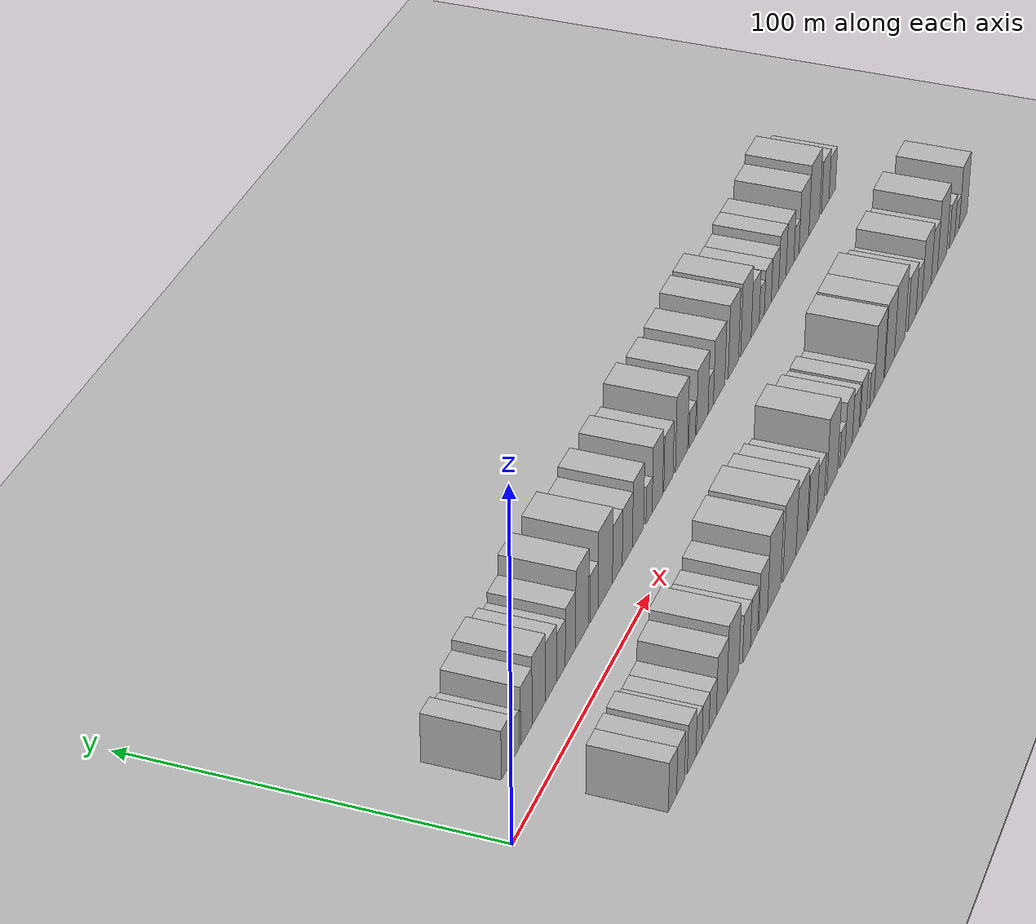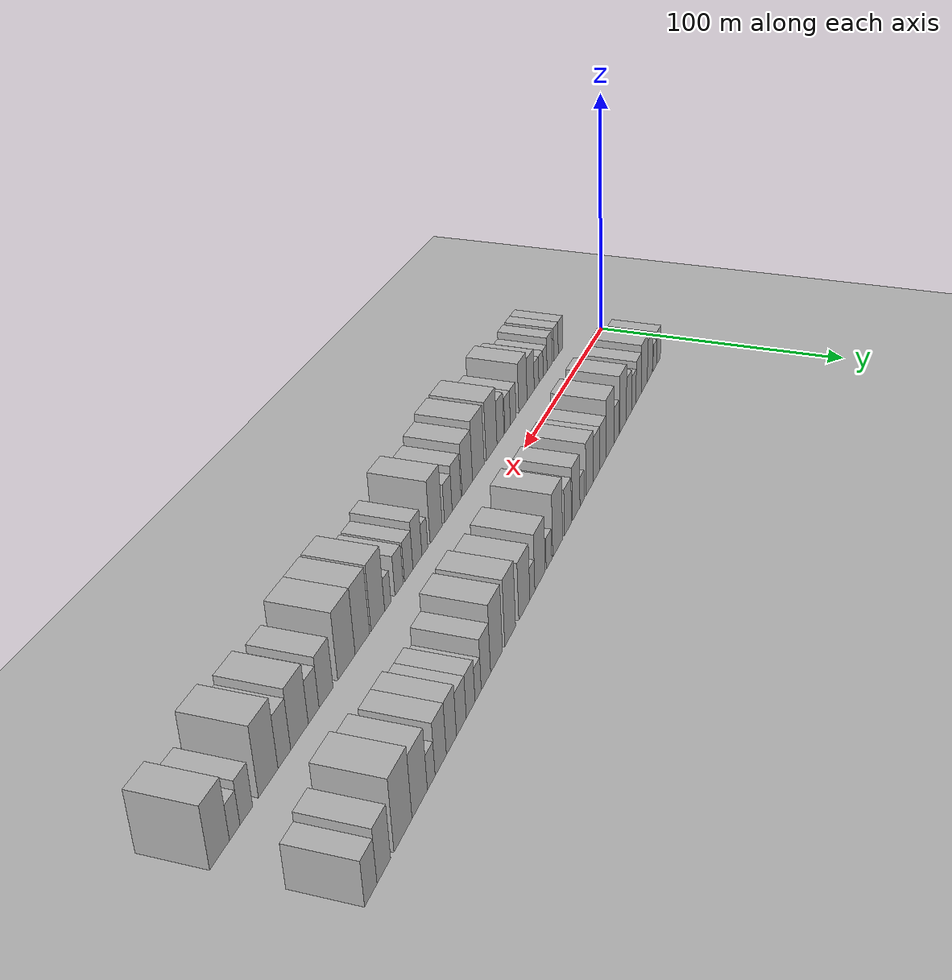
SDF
<?xml version="1.0" encoding="utf-8"?>

<sdf version="1.6">

   <world name="default">

      <gui fullscreen="0">

         <camera name="user_camera">

            <pose>-15 0 4.57585 0 0 0</pose>

            <view_controller>orbit</view_controller>

         </camera>

      </gui>

      <scene>

         <sky>

           <clouds>

             <speed>12</speed>

           </clouds>

         </sky>

         <ambient>0.4 0.4 0.4 1</ambient>

         <background>0.7 0.7 0.7 1</background>

         <shadows>1</shadows>

      </scene>

      <gravity>0 0 -9.8066</gravity>

      <magnetic_field>6e-06 2.3e-05 -4.2e-05</magnetic_field>

      <physics default="0" name="default_physics" type="ode">

         <ode>

            <solver>

               <type>quick</type>

               <iters>10</iters>

               <sor>1.0</sor>

               <use_dynamic_moi_rescaling>0</use_dynamic_moi_rescaling>

            </solver>

            <constraints>

               <cfm>0</cfm>

               <erp>0.2</erp>

               <contact_max_correcting_vel>100</contact_max_correcting_vel>

               <contact_surface_layer>0.001</contact_surface_layer>

            </constraints>

         </ode>

         <max_step_size>0.004</max_step_size>

         <real_time_factor>1</real_time_factor>

         <real_time_update_rate>250</real_time_update_rate>

      </physics>

      <light name="sun" type="directional">

         <cast_shadows>1</cast_shadows>

         <pose>0 0 10 0 0 0</pose>

         <diffuse>0.8 0.8 0.8 1</diffuse>

         <specular>0.2 0.2 0.2 1</specular>

         <attenuation>

            <range>1000</range>

            <constant>0.9</constant>

            <linear>0.01</linear>

            <quadratic>0.001</quadratic>

         </attenuation>

         <direction>-0.5 0.1 -0.9</direction>

      </light>

      <include>

         <name>ground_plane_1</name>

         <uri>model://HANNAS_ground_plane</uri>

         <pose>0 0 0  0 0 0</pose>

      </include>

      <include>

         <name>ground_plane_2</name>

         <uri>model://HANNAS_ground_plane</uri>

         <pose>100 0 0  0 0 0</pose>

      </include>

      <model name="building_1">

         <static>1</static>

         <pose frame="">23.2118 20.0000 0 0.000000 0.000000 1.570796</pose>

         <link name="link">

            <pose frame="">0 0 7.50 0 0 0</pose>

            <collision name="collision">

               <geometry>

                  <box>

                     <size>20.0000 6.4236 15.0000</size>

                  </box>

               </geometry>

               <max_contacts>10</max_contacts>

               <surface>

                  <contact>

                     <ode/>

                  </contact>

                  <bounce/>

                  <friction>

                     <torsional>

                        <ode/>

                     </torsional>

                     <ode/>

                  </friction>

               </surface>

            </collision>

            <visual name="visual">

               <cast_shadows>0</cast_shadows>

               <geometry>

                  <box>

                     <size>20.0000 6.4236 15.0000</size>

                  </box>

               </geometry>

               <material>

                  <script>

                     <uri>model://HANNAS_wall/materials/scripts</uri>

                     <uri>model://HANNAS_wall/materials/textures</uri>

                     <name>vrc/HANNAS_wall</name>

                  </script>

               </material>

            </visual>

            <self_collide>0</self_collide>

            <enable_wind>0</enable_wind>

            <kinematic>0</kinematic>

         </link>

      </model>

      <model name="building_2">

         <static>1</static>

         <pose frame="">29.3151 20.0000 0 0.000000 0.000000 1.570796</pose>

         <link name="link">

            <pose frame="">0 0 6.00 0 0 0</pose>

            <collision name="collision">

               <geometry>

                  <box>

                     <size>20.0000 5.7830 12.0000</size>

                  </box>

               </geometry>

               <max_contacts>10</max_contacts>

               <surface>

                  <contact>

                     <ode/>

                  </contact>

                  <bounce/>

                  <friction>

                     <torsional>

                        <ode/>

                     </torsional>

                     <ode/>

                  </friction>

               </surface>

            </collision>

            <visual name="visual">

               <cast_shadows>0</cast_shadows>

               <geometry>

                  <box>

                     <size>20.0000 5.7830 12.0000</size>

                  </box>

               </geometry>

               <material>

                  <script>

                     <uri>model://HANNAS_wall/materials/scripts</uri>

                     <uri>model://HANNAS_wall/materials/textures</uri>

                     <name>vrc/HANNAS_wall</name>

                  </script>

               </material>

            </visual>

            <self_collide>0</self_collide>

            <enable_wind>0</enable_wind>

            <kinematic>0</kinematic>

         </link>

      </model>

      <model name="building_3">

         <static>1</static>

         <pose frame="">37.1715 20.0000 0 0.000000 0.000000 1.570796</pose>

         <link name="link">

            <pose frame="">0 0 9.00 0 0 0</pose>

            <collision name="collision">

               <geometry>

                  <box>

                     <size>20.0000 7.9298 18.0000</size>

                  </box>

               </geometry>

               <max_contacts>10</max_contacts>

               <surface>

                  <contact>

                     <ode/>

                  </contact>

                  <bounce/>

                  <friction>

                     <torsional>

                        <ode/>

                     </torsional>

                     <ode/>

                  </friction>

               </surface>

            </collision>

            <visual name="visual">

               <cast_shadows>0</cast_shadows>

               <geometry>

                  <box>

                     <size>20.0000 7.9298 18.0000</size>

                  </box>

               </geometry>

               <material>

                  <script>

                     <uri>model://HANNAS_wall/materials/scripts</uri>

                     <uri>model://HANNAS_wall/materials/textures</uri>

                     <name>vrc/HANNAS_wall</name>

                  </script>

               </material>

            </visual>

            <self_collide>0</self_collide>

            <enable_wind>0</enable_wind>

            <kinematic>0</kinematic>

         </link>

      </model>

      <model name="building_4">

         <static>1</static>

         <pose frame="">45.9178 20.0000 0 0.000000 0.000000 1.570796</pose>

         <link name="link">

            <pose frame="">0 0 10.50 0 0 0</pose>

            <collision name="collision">

               <geometry>

                  <box>

                     <size>20.0000 9.5629 21.0000</size>

                  </box>

               </geometry>

               <max_contacts>10</max_contacts>

               <surface>

                  <contact>

                     <ode/>

                  </contact>

                  <bounce/>

                  <friction>

                     <torsional>

                        <ode/>

                     </torsional>

                     <ode/>

                  </friction>

               </surface>

            </collision>

            <visual name="visual">

               <cast_shadows>0</cast_shadows>

               <geometry>

                  <box>

                     <size>20.0000 9.5629 21.0000</size>

                  </box>

               </geometry>

               <material>

                  <script>

                     <uri>model://HANNAS_wall/materials/scripts</uri>

                     <uri>model://HANNAS_wall/materials/textures</uri>

                     <name>vrc/HANNAS_wall</name>

                  </script>

               </material>

            </visual>

            <self_collide>0</self_collide>

            <enable_wind>0</enable_wind>

            <kinematic>0</kinematic>

         </link>

      </model>

      <model name="building_5">

         <static>1</static>

         <pose frame="">54.6174 20.0000 0 0.000000 0.000000 1.570796</pose>

         <link name="link">

            <pose frame="">0 0 9.00 0 0 0</pose>

            <collision name="collision">

               <geometry>

                  <box>

                     <size>20.0000 7.8361 18.0000</size>

                  </box>

               </geometry>

               <max_contacts>10</max_contacts>

               <surface>

                  <contact>

                     <ode/>

                  </contact>

                  <bounce/>

                  <friction>

                     <torsional>

                        <ode/>

                     </torsional>

                     <ode/>

                  </friction>

               </surface>

            </collision>

            <visual name="visual">

               <cast_shadows>0</cast_shadows>

               <geometry>

                  <box>

                     <size>20.0000 7.8361 18.0000</size>

                  </box>

               </geometry>

               <material>

                  <script>

                     <uri>model://HANNAS_wall/materials/scripts</uri>

                     <uri>model://HANNAS_wall/materials/textures</uri>

                     <name>vrc/HANNAS_wall</name>

                  </script>

               </material>

            </visual>

            <self_collide>0</self_collide>

            <enable_wind>0</enable_wind>

            <kinematic>0</kinematic>

         </link>

      </model>

      <model name="building_6">

         <static>1</static>

         <pose frame="">61.7313 20.0000 0 0.000000 0.000000 1.570796</pose>

         <link name="link">

            <pose frame="">0 0 7.50 0 0 0</pose>

            <collision name="collision">

               <geometry>

                  <box>

                     <size>20.0000 6.3917 15.0000</size>

                  </box>

               </geometry>

               <max_contacts>10</max_contacts>

               <surface>

                  <contact>

                     <ode/>

                  </contact>

                  <bounce/>

                  <friction>

                     <torsional>

                        <ode/>

                     </torsional>

                     <ode/>

                  </friction>

               </surface>

            </collision>

            <visual name="visual">

               <cast_shadows>0</cast_shadows>

               <geometry>

                  <box>

                     <size>20.0000 6.3917 15.0000</size>

                  </box>

               </geometry>

               <material>

                  <script>

                     <uri>model://HANNAS_wall/materials/scripts</uri>

                     <uri>model://HANNAS_wall/materials/textures</uri>

                     <name>vrc/HANNAS_wall</name>

                  </script>

               </material>

            </visual>

            <self_collide>0</self_collide>

            <enable_wind>0</enable_wind>

            <kinematic>0</kinematic>

         </link>

      </model>

      <model name="building_7">

         <static>1</static>

         <pose frame="">68.7411 20.0000 0 0.000000 0.000000 1.570796</pose>

         <link name="link">

            <pose frame="">0 0 9.00 0 0 0</pose>

            <collision name="collision">

               <geometry>

                  <box>

                     <size>20.0000 7.6280 18.0000</size>

                  </box>

               </geometry>

               <max_contacts>10</max_contacts>

               <surface>

                  <contact>

                     <ode/>

                  </contact>

                  <bounce/>

                  <friction>

                     <torsional>

                        <ode/>

                     </torsional>

                     <ode/>

                  </friction>

               </surface>

            </collision>

            <visual name="visual">

               <cast_shadows>0</cast_shadows>

               <geometry>

                  <box>

                     <size>20.0000 7.6280 18.0000</size>

                  </box>

               </geometry>

               <material>

                  <script>

                     <uri>model://HANNAS_wall/materials/scripts</uri>

                     <uri>model://HANNAS_wall/materials/textures</uri>

                     <name>vrc/HANNAS_wall</name>

                  </script>

               </material>

            </visual>

            <self_collide>0</self_collide>

            <enable_wind>0</enable_wind>

            <kinematic>0</kinematic>

         </link>

      </model>

      <model name="building_8">

         <static>1</static>

         <pose frame="">77.4207 20.0000 0 0.000000 0.000000 1.570796</pose>

         <link name="link">

            <pose frame="">0 0 12.00 0 0 0</pose>

            <collision name="collision">

               <geometry>

                  <box>

                     <size>20.0000 9.7311 24.0000</size>

                  </box>

               </geometry>

               <max_contacts>10</max_contacts>

               <surface>

                  <contact>

                     <ode/>

                  </contact>

                  <bounce/>

                  <friction>

                     <torsional>

                        <ode/>

                     </torsional>

                     <ode/>

                  </friction>

               </surface>

            </collision>

            <visual name="visual">

               <cast_shadows>0</cast_shadows>

               <geometry>

                  <box>

                     <size>20.0000 9.7311 24.0000</size>

                  </box>

               </geometry>

               <material>

                  <script>

                     <uri>model://HANNAS_wall/materials/scripts</uri>

                     <uri>model://HANNAS_wall/materials/textures</uri>

                     <name>vrc/HANNAS_wall</name>

                  </script>

               </material>

            </visual>

            <self_collide>0</self_collide>

            <enable_wind>0</enable_wind>

            <kinematic>0</kinematic>

         </link>

      </model>

      <model name="building_9">

         <static>1</static>

         <pose frame="">86.3764 20.0000 0 0.000000 0.000000 1.570796</pose>

         <link name="link">

            <pose frame="">0 0 7.50 0 0 0</pose>

            <collision name="collision">

               <geometry>

                  <box>

                     <size>20.0000 6.1803 15.0000</size>

                  </box>

               </geometry>

               <max_contacts>10</max_contacts>

               <surface>

                  <contact>

                     <ode/>

                  </contact>

                  <bounce/>

                  <friction>

                     <torsional>

                        <ode/>

                     </torsional>

                     <ode/>

                  </friction>

               </surface>

            </collision>

            <visual name="visual">

               <cast_shadows>0</cast_shadows>

               <geometry>

                  <box>

                     <size>20.0000 6.1803 15.0000</size>

                  </box>

               </geometry>

               <material>

                  <script>

                     <uri>model://HANNAS_wall/materials/scripts</uri>

                     <uri>model://HANNAS_wall/materials/textures</uri>

                     <name>vrc/HANNAS_wall</name>

                  </script>

               </material>

            </visual>

            <self_collide>0</self_collide>

            <enable_wind>0</enable_wind>

            <kinematic>0</kinematic>

         </link>

      </model>

      <model name="building_10">

         <static>1</static>

         <pose frame="">95.0358 20.0000 0 0.000000 0.000000 1.570796</pose>

         <link name="link">

            <pose frame="">0 0 12.00 0 0 0</pose>

            <collision name="collision">

               <geometry>

                  <box>

                     <size>20.0000 11.1384 24.0000</size>

                  </box>

               </geometry>

               <max_contacts>10</max_contacts>

               <surface>

                  <contact>

                     <ode/>

                  </contact>

                  <bounce/>

                  <friction>

                     <torsional>

                        <ode/>

                     </torsional>

                     <ode/>

                  </friction>

               </surface>

            </collision>

            <visual name="visual">

               <cast_shadows>0</cast_shadows>

               <geometry>

                  <box>

                     <size>20.0000 11.1384 24.0000</size>

                  </box>

               </geometry>

               <material>

                  <script>

                     <uri>model://HANNAS_wall/materials/scripts</uri>

                     <uri>model://HANNAS_wall/materials/textures</uri>

                     <name>vrc/HANNAS_wall</name>

                  </script>

               </material>

            </visual>

            <self_collide>0</self_collide>

            <enable_wind>0</enable_wind>

            <kinematic>0</kinematic>

         </link>

      </model>

      <model name="building_11">

         <static>1</static>

         <pose frame="">104.4666 20.0000 0 0.000000 0.000000 1.570796</pose>

         <link name="link">

            <pose frame="">0 0 9.00 0 0 0</pose>

            <collision name="collision">

               <geometry>

                  <box>

                     <size>20.0000 7.7232 18.0000</size>

                  </box>

               </geometry>

               <max_contacts>10</max_contacts>

               <surface>

                  <contact>

                     <ode/>

                  </contact>

                  <bounce/>

                  <friction>

                     <torsional>

                        <ode/>

                     </torsional>

                     <ode/>

                  </friction>

               </surface>

            </collision>

            <visual name="visual">

               <cast_shadows>0</cast_shadows>

               <geometry>

                  <box>

                     <size>20.0000 7.7232 18.0000</size>

                  </box>

               </geometry>

               <material>

                  <script>

                     <uri>model://HANNAS_wall/materials/scripts</uri>

                     <uri>model://HANNAS_wall/materials/textures</uri>

                     <name>vrc/HANNAS_wall</name>

                  </script>

               </material>

            </visual>

            <self_collide>0</self_collide>

            <enable_wind>0</enable_wind>

            <kinematic>0</kinematic>

         </link>

      </model>

      <model name="building_12">

         <static>1</static>

         <pose frame="">112.3706 20.0000 0 0.000000 0.000000 1.570796</pose>

         <link name="link">

            <pose frame="">0 0 9.00 0 0 0</pose>

            <collision name="collision">

               <geometry>

                  <box>

                     <size>20.0000 8.0849 18.0000</size>

                  </box>

               </geometry>

               <max_contacts>10</max_contacts>

               <surface>

                  <contact>

                     <ode/>

                  </contact>

                  <bounce/>

                  <friction>

                     <torsional>

                        <ode/>

                     </torsional>

                     <ode/>

                  </friction>

               </surface>

            </collision>

            <visual name="visual">

               <cast_shadows>0</cast_shadows>

               <geometry>

                  <box>

                     <size>20.0000 8.0849 18.0000</size>

                  </box>

               </geometry>

               <material>

                  <script>

                     <uri>model://HANNAS_wall/materials/scripts</uri>

                     <uri>model://HANNAS_wall/materials/textures</uri>

                     <name>vrc/HANNAS_wall</name>

                  </script>

               </material>

            </visual>

            <self_collide>0</self_collide>

            <enable_wind>0</enable_wind>

            <kinematic>0</kinematic>

         </link>

      </model>

      <model name="building_13">

         <static>1</static>

         <pose frame="">120.9339 20.0000 0 0.000000 0.000000 1.570796</pose>

         <link name="link">

            <pose frame="">0 0 10.50 0 0 0</pose>

            <collision name="collision">

               <geometry>

                  <box>

                     <size>20.0000 9.0417 21.0000</size>

                  </box>

               </geometry>

               <max_contacts>10</max_contacts>

               <surface>

                  <contact>

                     <ode/>

                  </contact>

                  <bounce/>

                  <friction>

                     <torsional>

                        <ode/>

                     </torsional>

                     <ode/>

                  </friction>

               </surface>

            </collision>

            <visual name="visual">

               <cast_shadows>0</cast_shadows>

               <geometry>

                  <box>

                     <size>20.0000 9.0417 21.0000</size>

                  </box>

               </geometry>

               <material>

                  <script>

                     <uri>model://HANNAS_wall/materials/scripts</uri>

                     <uri>model://HANNAS_wall/materials/textures</uri>

                     <name>vrc/HANNAS_wall</name>

                  </script>

               </material>

            </visual>

            <self_collide>0</self_collide>

            <enable_wind>0</enable_wind>

            <kinematic>0</kinematic>

         </link>

      </model>

      <model name="building_14">

         <static>1</static>

         <pose frame="">129.9616 20.0000 0 0.000000 0.000000 1.570796</pose>

         <link name="link">

            <pose frame="">0 0 6.00 0 0 0</pose>

            <collision name="collision">

               <geometry>

                  <box>

                     <size>20.0000 5.0136 12.0000</size>

                  </box>

               </geometry>

               <max_contacts>10</max_contacts>

               <surface>

                  <contact>

                     <ode/>

                  </contact>

                  <bounce/>

                  <friction>

                     <torsional>

                        <ode/>

                     </torsional>

                     <ode/>

                  </friction>

               </surface>

            </collision>

            <visual name="visual">

               <cast_shadows>0</cast_shadows>

               <geometry>

                  <box>

                     <size>20.0000 5.0136 12.0000</size>

                  </box>

               </geometry>

               <material>

                  <script>

                     <uri>model://HANNAS_wall/materials/scripts</uri>

                     <uri>model://HANNAS_wall/materials/textures</uri>

                     <name>vrc/HANNAS_wall</name>

                  </script>

               </material>

            </visual>

            <self_collide>0</self_collide>

            <enable_wind>0</enable_wind>

            <kinematic>0</kinematic>

         </link>

      </model>

      <model name="building_15">

         <static>1</static>

         <pose frame="">136.8514 20.0000 0 0.000000 0.000000 1.570796</pose>

         <link name="link">

            <pose frame="">0 0 10.50 0 0 0</pose>

            <collision name="collision">

               <geometry>

                  <box>

                     <size>20.0000 8.7661 21.0000</size>

                  </box>

               </geometry>

               <max_contacts>10</max_contacts>

               <surface>

                  <contact>

                     <ode/>

                  </contact>

                  <bounce/>

                  <friction>

                     <torsional>

                        <ode/>

                     </torsional>

                     <ode/>

                  </friction>

               </surface>

            </collision>

            <visual name="visual">

               <cast_shadows>0</cast_shadows>

               <geometry>

                  <box>

                     <size>20.0000 8.7661 21.0000</size>

                  </box>

               </geometry>

               <material>

                  <script>

                     <uri>model://HANNAS_wall/materials/scripts</uri>

                     <uri>model://HANNAS_wall/materials/textures</uri>

                     <name>vrc/HANNAS_wall</name>

                  </script>

               </material>

            </visual>

            <self_collide>0</self_collide>

            <enable_wind>0</enable_wind>

            <kinematic>0</kinematic>

         </link>

      </model>

      <model name="building_16">

         <static>1</static>

         <pose frame="">146.1345 20.0000 0 0.000000 0.000000 1.570796</pose>

         <link name="link">

            <pose frame="">0 0 9.00 0 0 0</pose>

            <collision name="collision">

               <geometry>

                  <box>

                     <size>20.0000 7.8002 18.0000</size>

                  </box>

               </geometry>

               <max_contacts>10</max_contacts>

               <surface>

                  <contact>

                     <ode/>

                  </contact>

                  <bounce/>

                  <friction>

                     <torsional>

                        <ode/>

                     </torsional>

                     <ode/>

                  </friction>

               </surface>

            </collision>

            <visual name="visual">

               <cast_shadows>0</cast_shadows>

               <geometry>

                  <box>

                     <size>20.0000 7.8002 18.0000</size>

                  </box>

               </geometry>

               <material>

                  <script>

                     <uri>model://HANNAS_wall/materials/scripts</uri>

                     <uri>model://HANNAS_wall/materials/textures</uri>

                     <name>vrc/HANNAS_wall</name>

                  </script>

               </material>

            </visual>

            <self_collide>0</self_collide>

            <enable_wind>0</enable_wind>

            <kinematic>0</kinematic>

         </link>

      </model>

      <model name="building_17">

         <static>1</static>

         <pose frame="">157.3124 20.0000 0 0.000000 0.000000 1.570796</pose>

         <link name="link">

            <pose frame="">0 0 12.00 0 0 0</pose>

            <collision name="collision">

               <geometry>

                  <box>

                     <size>20.0000 10.5557 24.0000</size>

                  </box>

               </geometry>

               <max_contacts>10</max_contacts>

               <surface>

                  <contact>

                     <ode/>

                  </contact>

                  <bounce/>

                  <friction>

                     <torsional>

                        <ode/>

                     </torsional>

                     <ode/>

                  </friction>

               </surface>

            </collision>

            <visual name="visual">

               <cast_shadows>0</cast_shadows>

               <geometry>

                  <box>

                     <size>20.0000 10.5557 24.0000</size>

                  </box>

               </geometry>

               <material>

                  <script>

                     <uri>model://HANNAS_wall/materials/scripts</uri>

                     <uri>model://HANNAS_wall/materials/textures</uri>

                     <name>vrc/HANNAS_wall</name>

                  </script>

               </material>

            </visual>

            <self_collide>0</self_collide>

            <enable_wind>0</enable_wind>

            <kinematic>0</kinematic>

         </link>

      </model>

      <model name="building_18">

         <static>1</static>

         <pose frame="">166.4663 20.0000 0 0.000000 0.000000 1.570796</pose>

         <link name="link">

            <pose frame="">0 0 6.00 0 0 0</pose>

            <collision name="collision">

               <geometry>

                  <box>

                     <size>20.0000 5.7520 12.0000</size>

                  </box>

               </geometry>

               <max_contacts>10</max_contacts>

               <surface>

                  <contact>

                     <ode/>

                  </contact>

                  <bounce/>

                  <friction>

                     <torsional>

                        <ode/>

                     </torsional>

                     <ode/>

                  </friction>

               </surface>

            </collision>

            <visual name="visual">

               <cast_shadows>0</cast_shadows>

               <geometry>

                  <box>

                     <size>20.0000 5.7520 12.0000</size>

                  </box>

               </geometry>

               <material>

                  <script>

                     <uri>model://HANNAS_wall/materials/scripts</uri>

                     <uri>model://HANNAS_wall/materials/textures</uri>

                     <name>vrc/HANNAS_wall</name>

                  </script>

               </material>

            </visual>

            <self_collide>0</self_collide>

            <enable_wind>0</enable_wind>

            <kinematic>0</kinematic>

         </link>

      </model>

      <model name="building_19">

         <static>1</static>

         <pose frame="">175.5122 20.0000 0 0.000000 0.000000 1.570796</pose>

         <link name="link">

            <pose frame="">0 0 10.50 0 0 0</pose>

            <collision name="collision">

               <geometry>

                  <box>

                     <size>20.0000 10.3398 21.0000</size>

                  </box>

               </geometry>

               <max_contacts>10</max_contacts>

               <surface>

                  <contact>

                     <ode/>

                  </contact>

                  <bounce/>

                  <friction>

                     <torsional>

                        <ode/>

                     </torsional>

                     <ode/>

                  </friction>

               </surface>

            </collision>

            <visual name="visual">

               <cast_shadows>0</cast_shadows>

               <geometry>

                  <box>

                     <size>20.0000 10.3398 21.0000</size>

                  </box>

               </geometry>

               <material>

                  <script>

                     <uri>model://HANNAS_wall/materials/scripts</uri>

                     <uri>model://HANNAS_wall/materials/textures</uri>

                     <name>vrc/HANNAS_wall</name>

                  </script>

               </material>

            </visual>

            <self_collide>0</self_collide>

            <enable_wind>0</enable_wind>

            <kinematic>0</kinematic>

         </link>

      </model>

      <model name="building_20">

         <static>1</static>

         <pose frame="">183.0930 20.0000 0 0.000000 0.000000 1.570796</pose>

         <link name="link">

            <pose frame="">0 0 6.00 0 0 0</pose>

            <collision name="collision">

               <geometry>

                  <box>

                     <size>20.0000 4.8217 12.0000</size>

                  </box>

               </geometry>

               <max_contacts>10</max_contacts>

               <surface>

                  <contact>

                     <ode/>

                  </contact>

                  <bounce/>

                  <friction>

                     <torsional>

                        <ode/>

                     </torsional>

                     <ode/>

                  </friction>

               </surface>

            </collision>

            <visual name="visual">

               <cast_shadows>0</cast_shadows>

               <geometry>

                  <box>

                     <size>20.0000 4.8217 12.0000</size>

                  </box>

               </geometry>

               <material>

                  <script>

                     <uri>model://HANNAS_wall/materials/scripts</uri>

                     <uri>model://HANNAS_wall/materials/textures</uri>

                     <name>vrc/HANNAS_wall</name>

                  </script>

               </material>

            </visual>

            <self_collide>0</self_collide>

            <enable_wind>0</enable_wind>

            <kinematic>0</kinematic>

         </link>

      </model>

      <model name="building_21">

         <static>1</static>

         <pose frame="">190.7196 20.0000 0 0.000000 0.000000 1.570796</pose>

         <link name="link">

            <pose frame="">0 0 10.50 0 0 0</pose>

            <collision name="collision">

               <geometry>

                  <box>

                     <size>20.0000 10.4315 21.0000</size>

                  </box>

               </geometry>

               <max_contacts>10</max_contacts>

               <surface>

                  <contact>

                     <ode/>

                  </contact>

                  <bounce/>

                  <friction>

                     <torsional>

                        <ode/>

                     </torsional>

                     <ode/>

                  </friction>

               </surface>

            </collision>

            <visual name="visual">

               <cast_shadows>0</cast_shadows>

               <geometry>

                  <box>

                     <size>20.0000 10.4315 21.0000</size>

                  </box>

               </geometry>

               <material>

                  <script>

                     <uri>model://HANNAS_wall/materials/scripts</uri>

                     <uri>model://HANNAS_wall/materials/textures</uri>

                     <name>vrc/HANNAS_wall</name>

                  </script>

               </material>

            </visual>

            <self_collide>0</self_collide>

            <enable_wind>0</enable_wind>

            <kinematic>0</kinematic>

         </link>

      </model>

      <model name="building_22">

         <static>1</static>

         <pose frame="">203.7811 20.0000 0 0.000000 0.000000 1.570796</pose>

         <link name="link">

            <pose frame="">0 0 12.00 0 0 0</pose>

            <collision name="collision">

               <geometry>

                  <box>

                     <size>20.0000 9.6916 24.0000</size>

                  </box>

               </geometry>

               <max_contacts>10</max_contacts>

               <surface>

                  <contact>

                     <ode/>

                  </contact>

                  <bounce/>

                  <friction>

                     <torsional>

                        <ode/>

                     </torsional>

                     <ode/>

                  </friction>

               </surface>

            </collision>

            <visual name="visual">

               <cast_shadows>0</cast_shadows>

               <geometry>

                  <box>

                     <size>20.0000 9.6916 24.0000</size>

                  </box>

               </geometry>

               <material>

                  <script>

                     <uri>model://HANNAS_wall/materials/scripts</uri>

                     <uri>model://HANNAS_wall/materials/textures</uri>

                     <name>vrc/HANNAS_wall</name>

                  </script>

               </material>

            </visual>

            <self_collide>0</self_collide>

            <enable_wind>0</enable_wind>

            <kinematic>0</kinematic>

         </link>

      </model>

      <model name="building_23">

         <static>1</static>

         <pose frame="">215.6560 20.0000 0 0.000000 0.000000 1.570796</pose>

         <link name="link">

            <pose frame="">0 0 12.00 0 0 0</pose>

            <collision name="collision">

               <geometry>

                  <box>

                     <size>20.0000 10.0581 24.0000</size>

                  </box>

               </geometry>

               <max_contacts>10</max_contacts>

               <surface>

                  <contact>

                     <ode/>

                  </contact>

                  <bounce/>

                  <friction>

                     <torsional>

                        <ode/>

                     </torsional>

                     <ode/>

                  </friction>

               </surface>

            </collision>

            <visual name="visual">

               <cast_shadows>0</cast_shadows>

               <geometry>

                  <box>

                     <size>20.0000 10.0581 24.0000</size>

                  </box>

               </geometry>

               <material>

                  <script>

                     <uri>model://HANNAS_wall/materials/scripts</uri>

                     <uri>model://HANNAS_wall/materials/textures</uri>

                     <name>vrc/HANNAS_wall</name>

                  </script>

               </material>

            </visual>

            <self_collide>0</self_collide>

            <enable_wind>0</enable_wind>

            <kinematic>0</kinematic>

         </link>

      </model>

      <model name="building_24">

         <static>1</static>

         <pose frame="">224.5340 20.0000 0 0.000000 0.000000 1.570796</pose>

         <link name="link">

            <pose frame="">0 0 9.00 0 0 0</pose>

            <collision name="collision">

               <geometry>

                  <box>

                     <size>20.0000 7.6978 18.0000</size>

                  </box>

               </geometry>

               <max_contacts>10</max_contacts>

               <surface>

                  <contact>

                     <ode/>

                  </contact>

                  <bounce/>

                  <friction>

                     <torsional>

                        <ode/>

                     </torsional>

                     <ode/>

                  </friction>

               </surface>

            </collision>

            <visual name="visual">

               <cast_shadows>0</cast_shadows>

               <geometry>

                  <box>

                     <size>20.0000 7.6978 18.0000</size>

                  </box>

               </geometry>

               <material>

                  <script>

                     <uri>model://HANNAS_wall/materials/scripts</uri>

                     <uri>model://HANNAS_wall/materials/textures</uri>

                     <name>vrc/HANNAS_wall</name>

                  </script>

               </material>

            </visual>

            <self_collide>0</self_collide>

            <enable_wind>0</enable_wind>

            <kinematic>0</kinematic>

         </link>

      </model>

      <model name="building_25">

         <static>1</static>

         <pose frame="">230.8734 20.0000 0 0.000000 0.000000 1.570796</pose>

         <link name="link">

            <pose frame="">0 0 6.00 0 0 0</pose>

            <collision name="collision">

               <geometry>

                  <box>

                     <size>20.0000 4.9810 12.0000</size>

                  </box>

               </geometry>

               <max_contacts>10</max_contacts>

               <surface>

                  <contact>

                     <ode/>

                  </contact>

                  <bounce/>

                  <friction>

                     <torsional>

                        <ode/>

                     </torsional>

                     <ode/>

                  </friction>

               </surface>

            </collision>

            <visual name="visual">

               <cast_shadows>0</cast_shadows>

               <geometry>

                  <box>

                     <size>20.0000 4.9810 12.0000</size>

                  </box>

               </geometry>

               <material>

                  <script>

                     <uri>model://HANNAS_wall/materials/scripts</uri>

                     <uri>model://HANNAS_wall/materials/textures</uri>

                     <name>vrc/HANNAS_wall</name>

                  </script>

               </material>

            </visual>

            <self_collide>0</self_collide>

            <enable_wind>0</enable_wind>

            <kinematic>0</kinematic>

         </link>

      </model>

      <model name="building_26">

         <static>1</static>

         <pose frame="">236.7851 20.0000 0 0.000000 0.000000 1.570796</pose>

         <link name="link">

            <pose frame="">0 0 7.50 0 0 0</pose>

            <collision name="collision">

               <geometry>

                  <box>

                     <size>20.0000 6.8425 15.0000</size>

                  </box>

               </geometry>

               <max_contacts>10</max_contacts>

               <surface>

                  <contact>

                     <ode/>

                  </contact>

                  <bounce/>

                  <friction>

                     <torsional>

                        <ode/>

                     </torsional>

                     <ode/>

                  </friction>

               </surface>

            </collision>

            <visual name="visual">

               <cast_shadows>0</cast_shadows>

               <geometry>

                  <box>

                     <size>20.0000 6.8425 15.0000</size>

                  </box>

               </geometry>

               <material>

                  <script>

                     <uri>model://HANNAS_wall/materials/scripts</uri>

                     <uri>model://HANNAS_wall/materials/textures</uri>

                     <name>vrc/HANNAS_wall</name>

                  </script>

               </material>

            </visual>

            <self_collide>0</self_collide>

            <enable_wind>0</enable_wind>

            <kinematic>0</kinematic>

         </link>

      </model>

      <model name="building_27">

         <static>1</static>

         <pose frame="">243.8890 20.0000 0 0.000000 0.000000 1.570796</pose>

         <link name="link">

            <pose frame="">0 0 7.50 0 0 0</pose>

            <collision name="collision">

               <geometry>

                  <box>

                     <size>20.0000 7.3652 15.0000</size>

                  </box>

               </geometry>

               <max_contacts>10</max_contacts>

               <surface>

                  <contact>

                     <ode/>

                  </contact>

                  <bounce/>

                  <friction>

                     <torsional>

                        <ode/>

                     </torsional>

                     <ode/>

                  </friction>

               </surface>

            </collision>

            <visual name="visual">

               <cast_shadows>0</cast_shadows>

               <geometry>

                  <box>

                     <size>20.0000 7.3652 15.0000</size>

                  </box>

               </geometry>

               <material>

                  <script>

                     <uri>model://HANNAS_wall/materials/scripts</uri>

                     <uri>model://HANNAS_wall/materials/textures</uri>

                     <name>vrc/HANNAS_wall</name>

                  </script>

               </material>

            </visual>

            <self_collide>0</self_collide>

            <enable_wind>0</enable_wind>

            <kinematic>0</kinematic>

         </link>

      </model>

      <model name="building_28">

         <static>1</static>

         <pose frame="">251.2797 20.0000 0 0.000000 0.000000 1.570796</pose>

         <link name="link">

            <pose frame="">0 0 9.00 0 0 0</pose>

            <collision name="collision">

               <geometry>

                  <box>

                     <size>20.0000 7.4162 18.0000</size>

                  </box>

               </geometry>

               <max_contacts>10</max_contacts>

               <surface>

                  <contact>

                     <ode/>

                  </contact>

                  <bounce/>

                  <friction>

                     <torsional>

                        <ode/>

                     </torsional>

                     <ode/>

                  </friction>

               </surface>

            </collision>

            <visual name="visual">

               <cast_shadows>0</cast_shadows>

               <geometry>

                  <box>

                     <size>20.0000 7.4162 18.0000</size>

                  </box>

               </geometry>

               <material>

                  <script>

                     <uri>model://HANNAS_wall/materials/scripts</uri>

                     <uri>model://HANNAS_wall/materials/textures</uri>

                     <name>vrc/HANNAS_wall</name>

                  </script>

               </material>

            </visual>

            <self_collide>0</self_collide>

            <enable_wind>0</enable_wind>

            <kinematic>0</kinematic>

         </link>

      </model>

      <model name="building_29">

         <static>1</static>

         <pose frame="">258.9793 20.0000 0 0.000000 0.000000 1.570796</pose>

         <link name="link">

            <pose frame="">0 0 9.00 0 0 0</pose>

            <collision name="collision">

               <geometry>

                  <box>

                     <size>20.0000 7.9831 18.0000</size>

                  </box>

               </geometry>

               <max_contacts>10</max_contacts>

               <surface>

                  <contact>

                     <ode/>

                  </contact>

                  <bounce/>

                  <friction>

                     <torsional>

                        <ode/>

                     </torsional>

                     <ode/>

                  </friction>

               </surface>

            </collision>

            <visual name="visual">

               <cast_shadows>0</cast_shadows>

               <geometry>

                  <box>

                     <size>20.0000 7.9831 18.0000</size>

                  </box>

               </geometry>

               <material>

                  <script>

                     <uri>model://HANNAS_wall/materials/scripts</uri>

                     <uri>model://HANNAS_wall/materials/textures</uri>

                     <name>vrc/HANNAS_wall</name>

                  </script>

               </material>

            </visual>

            <self_collide>0</self_collide>

            <enable_wind>0</enable_wind>

            <kinematic>0</kinematic>

         </link>

      </model>

      <model name="building_30">

         <static>1</static>

         <pose frame="">265.6253 20.0000 0 0.000000 0.000000 1.570796</pose>

         <link name="link">

            <pose frame="">0 0 6.00 0 0 0</pose>

            <collision name="collision">

               <geometry>

                  <box>

                     <size>20.0000 5.3088 12.0000</size>

                  </box>

               </geometry>

               <max_contacts>10</max_contacts>

               <surface>

                  <contact>

                     <ode/>

                  </contact>

                  <bounce/>

                  <friction>

                     <torsional>

                        <ode/>

                     </torsional>

                     <ode/>

                  </friction>

               </surface>

            </collision>

            <visual name="visual">

               <cast_shadows>0</cast_shadows>

               <geometry>

                  <box>

                     <size>20.0000 5.3088 12.0000</size>

                  </box>

               </geometry>

               <material>

                  <script>

                     <uri>model://HANNAS_wall/materials/scripts</uri>

                     <uri>model://HANNAS_wall/materials/textures</uri>

                     <name>vrc/HANNAS_wall</name>

                  </script>

               </material>

            </visual>

            <self_collide>0</self_collide>

            <enable_wind>0</enable_wind>

            <kinematic>0</kinematic>

         </link>

      </model>

      <model name="building_31">

         <static>1</static>

         <pose frame="">273.3707 20.0000 0 0.000000 0.000000 1.570796</pose>

         <link name="link">

            <pose frame="">0 0 10.50 0 0 0</pose>

            <collision name="collision">

               <geometry>

                  <box>

                     <size>20.0000 10.1820 21.0000</size>

                  </box>

               </geometry>

               <max_contacts>10</max_contacts>

               <surface>

                  <contact>

                     <ode/>

                  </contact>

                  <bounce/>

                  <friction>

                     <torsional>

                        <ode/>

                     </torsional>

                     <ode/>

                  </friction>

               </surface>

            </collision>

            <visual name="visual">

               <cast_shadows>0</cast_shadows>

               <geometry>

                  <box>

                     <size>20.0000 10.1820 21.0000</size>

                  </box>

               </geometry>

               <material>

                  <script>

                     <uri>model://HANNAS_wall/materials/scripts</uri>

                     <uri>model://HANNAS_wall/materials/textures</uri>

                     <name>vrc/HANNAS_wall</name>

                  </script>

               </material>

            </visual>

            <self_collide>0</self_collide>

            <enable_wind>0</enable_wind>

            <kinematic>0</kinematic>

         </link>

      </model>

      <model name="building_32">

         <static>1</static>

         <pose frame="">284.1615 20.0000 0 0.000000 0.000000 1.570796</pose>

         <link name="link">

            <pose frame="">0 0 12.00 0 0 0</pose>

            <collision name="collision">

               <geometry>

                  <box>

                     <size>20.0000 11.3996 24.0000</size>

                  </box>

               </geometry>

               <max_contacts>10</max_contacts>

               <surface>

                  <contact>

                     <ode/>

                  </contact>

                  <bounce/>

                  <friction>

                     <torsional>

                        <ode/>

                     </torsional>

                     <ode/>

                  </friction>

               </surface>

            </collision>

            <visual name="visual">

               <cast_shadows>0</cast_shadows>

               <geometry>

                  <box>

                     <size>20.0000 11.3996 24.0000</size>

                  </box>

               </geometry>

               <material>

                  <script>

                     <uri>model://HANNAS_wall/materials/scripts</uri>

                     <uri>model://HANNAS_wall/materials/textures</uri>

                     <name>vrc/HANNAS_wall</name>

                  </script>

               </material>

            </visual>

            <self_collide>0</self_collide>

            <enable_wind>0</enable_wind>

            <kinematic>0</kinematic>

         </link>

      </model>

      <model name="building_33">

         <static>1</static>

         <pose frame="">295.9186 20.0000 0 0.000000 0.000000 1.570796</pose>

         <link name="link">

            <pose frame="">0 0 9.00 0 0 0</pose>

            <collision name="collision">

               <geometry>

                  <box>

                     <size>20.0000 8.1147 18.0000</size>

                  </box>

               </geometry>

               <max_contacts>10</max_contacts>

               <surface>

                  <contact>

                     <ode/>

                  </contact>

                  <bounce/>

                  <friction>

                     <torsional>

                        <ode/>

                     </torsional>

                     <ode/>

                  </friction>

               </surface>

            </collision>

            <visual name="visual">

               <cast_shadows>0</cast_shadows>

               <geometry>

                  <box>

                     <size>20.0000 8.1147 18.0000</size>

                  </box>

               </geometry>

               <material>

                  <script>

                     <uri>model://HANNAS_wall/materials/scripts</uri>

                     <uri>model://HANNAS_wall/materials/textures</uri>

                     <name>vrc/HANNAS_wall</name>

                  </script>

               </material>

            </visual>

            <self_collide>0</self_collide>

            <enable_wind>0</enable_wind>

            <kinematic>0</kinematic>

         </link>

      </model>

      <model name="building_34">

         <static>1</static>

         <pose frame="">303.5557 20.0000 0 0.000000 0.000000 1.570796</pose>

         <link name="link">

            <pose frame="">0 0 7.50 0 0 0</pose>

            <collision name="collision">

               <geometry>

                  <box>

                     <size>20.0000 7.1594 15.0000</size>

                  </box>

               </geometry>

               <max_contacts>10</max_contacts>

               <surface>

                  <contact>

                     <ode/>

                  </contact>

                  <bounce/>

                  <friction>

                     <torsional>

                        <ode/>

                     </torsional>

                     <ode/>

                  </friction>

               </surface>

            </collision>

            <visual name="visual">

               <cast_shadows>0</cast_shadows>

               <geometry>

                  <box>

                     <size>20.0000 7.1594 15.0000</size>

                  </box>

               </geometry>

               <material>

                  <script>

                     <uri>model://HANNAS_wall/materials/scripts</uri>

                     <uri>model://HANNAS_wall/materials/textures</uri>

                     <name>vrc/HANNAS_wall</name>

                  </script>

               </material>

            </visual>

            <self_collide>0</self_collide>

            <enable_wind>0</enable_wind>

            <kinematic>0</kinematic>

         </link>

      </model>

      <model name="building_35">

         <static>1</static>

         <pose frame="">25.0960 -20.0000 0 0.000000 0.000000 1.570796</pose>

         <link name="link">

            <pose frame="">0 0 7.50 0 0 0</pose>

            <collision name="collision">

               <geometry>

                  <box>

                     <size>20.0000 6.1920 15.0000</size>

                  </box>

               </geometry>

               <max_contacts>10</max_contacts>

               <surface>

                  <contact>

                     <ode/>

                  </contact>

                  <bounce/>

                  <friction>

                     <torsional>

                        <ode/>

                     </torsional>

                     <ode/>

                  </friction>

               </surface>

            </collision>

            <visual name="visual">

               <cast_shadows>0</cast_shadows>

               <geometry>

                  <box>

                     <size>20.0000 6.1920 15.0000</size>

                  </box>

               </geometry>

               <material>

                  <script>

                     <uri>model://HANNAS_wall/materials/scripts</uri>

                     <uri>model://HANNAS_wall/materials/textures</uri>

                     <name>vrc/HANNAS_wall</name>

                  </script>

               </material>

            </visual>

            <self_collide>0</self_collide>

            <enable_wind>0</enable_wind>

            <kinematic>0</kinematic>

         </link>

      </model>

      <model name="building_36">

         <static>1</static>

         <pose frame="">31.2714 -20.0000 0 0.000000 0.000000 1.570796</pose>

         <link name="link">

            <pose frame="">0 0 7.50 0 0 0</pose>

            <collision name="collision">

               <geometry>

                  <box>

                     <size>20.0000 6.1588 15.0000</size>

                  </box>

               </geometry>

               <max_contacts>10</max_contacts>

               <surface>

                  <contact>

                     <ode/>

                  </contact>

                  <bounce/>

                  <friction>

                     <torsional>

                        <ode/>

                     </torsional>

                     <ode/>

                  </friction>

               </surface>

            </collision>

            <visual name="visual">

               <cast_shadows>0</cast_shadows>

               <geometry>

                  <box>

                     <size>20.0000 6.1588 15.0000</size>

                  </box>

               </geometry>

               <material>

                  <script>

                     <uri>model://HANNAS_wall/materials/scripts</uri>

                     <uri>model://HANNAS_wall/materials/textures</uri>

                     <name>vrc/HANNAS_wall</name>

                  </script>

               </material>

            </visual>

            <self_collide>0</self_collide>

            <enable_wind>0</enable_wind>

            <kinematic>0</kinematic>

         </link>

      </model>

      <model name="building_37">

         <static>1</static>

         <pose frame="">39.6636 -20.0000 0 0.000000 0.000000 1.570796</pose>

         <link name="link">

            <pose frame="">0 0 7.50 0 0 0</pose>

            <collision name="collision">

               <geometry>

                  <box>

                     <size>20.0000 6.6255 15.0000</size>

                  </box>

               </geometry>

               <max_contacts>10</max_contacts>

               <surface>

                  <contact>

                     <ode/>

                  </contact>

                  <bounce/>

                  <friction>

                     <torsional>

                        <ode/>

                     </torsional>

                     <ode/>

                  </friction>

               </surface>

            </collision>

            <visual name="visual">

               <cast_shadows>0</cast_shadows>

               <geometry>

                  <box>

                     <size>20.0000 6.6255 15.0000</size>

                  </box>

               </geometry>

               <material>

                  <script>

                     <uri>model://HANNAS_wall/materials/scripts</uri>

                     <uri>model://HANNAS_wall/materials/textures</uri>

                     <name>vrc/HANNAS_wall</name>

                  </script>

               </material>

            </visual>

            <self_collide>0</self_collide>

            <enable_wind>0</enable_wind>

            <kinematic>0</kinematic>

         </link>

      </model>

      <model name="building_38">

         <static>1</static>

         <pose frame="">45.3991 -20.0000 0 0.000000 0.000000 1.570796</pose>

         <link name="link">

            <pose frame="">0 0 6.00 0 0 0</pose>

            <collision name="collision">

               <geometry>

                  <box>

                     <size>20.0000 4.8455 12.0000</size>

                  </box>

               </geometry>

               <max_contacts>10</max_contacts>

               <surface>

                  <contact>

                     <ode/>

                  </contact>

                  <bounce/>

                  <friction>

                     <torsional>

                        <ode/>

                     </torsional>

                     <ode/>

                  </friction>

               </surface>

            </collision>

            <visual name="visual">

               <cast_shadows>0</cast_shadows>

               <geometry>

                  <box>

                     <size>20.0000 4.8455 12.0000</size>

                  </box>

               </geometry>

               <material>

                  <script>

                     <uri>model://HANNAS_wall/materials/scripts</uri>

                     <uri>model://HANNAS_wall/materials/textures</uri>

                     <name>vrc/HANNAS_wall</name>

                  </script>

               </material>

            </visual>

            <self_collide>0</self_collide>

            <enable_wind>0</enable_wind>

            <kinematic>0</kinematic>

         </link>

      </model>

      <model name="building_39">

         <static>1</static>

         <pose frame="">50.5723 -20.0000 0 0.000000 0.000000 1.570796</pose>

         <link name="link">

            <pose frame="">0 0 6.00 0 0 0</pose>

            <collision name="collision">

               <geometry>

                  <box>

                     <size>20.0000 5.5010 12.0000</size>

                  </box>

               </geometry>

               <max_contacts>10</max_contacts>

               <surface>

                  <contact>

                     <ode/>

                  </contact>

                  <bounce/>

                  <friction>

                     <torsional>

                        <ode/>

                     </torsional>

                     <ode/>

                  </friction>

               </surface>

            </collision>

            <visual name="visual">

               <cast_shadows>0</cast_shadows>

               <geometry>

                  <box>

                     <size>20.0000 5.5010 12.0000</size>

                  </box>

               </geometry>

               <material>

                  <script>

                     <uri>model://HANNAS_wall/materials/scripts</uri>

                     <uri>model://HANNAS_wall/materials/textures</uri>

                     <name>vrc/HANNAS_wall</name>

                  </script>

               </material>

            </visual>

            <self_collide>0</self_collide>

            <enable_wind>0</enable_wind>

            <kinematic>0</kinematic>

         </link>

      </model>

      <model name="building_40">

         <static>1</static>

         <pose frame="">56.1987 -20.0000 0 0.000000 0.000000 1.570796</pose>

         <link name="link">

            <pose frame="">0 0 6.00 0 0 0</pose>

            <collision name="collision">

               <geometry>

                  <box>

                     <size>20.0000 5.7517 12.0000</size>

                  </box>

               </geometry>

               <max_contacts>10</max_contacts>

               <surface>

                  <contact>

                     <ode/>

                  </contact>

                  <bounce/>

                  <friction>

                     <torsional>

                        <ode/>

                     </torsional>

                     <ode/>

                  </friction>

               </surface>

            </collision>

            <visual name="visual">

               <cast_shadows>0</cast_shadows>

               <geometry>

                  <box>

                     <size>20.0000 5.7517 12.0000</size>

                  </box>

               </geometry>

               <material>

                  <script>

                     <uri>model://HANNAS_wall/materials/scripts</uri>

                     <uri>model://HANNAS_wall/materials/textures</uri>

                     <name>vrc/HANNAS_wall</name>

                  </script>

               </material>

            </visual>

            <self_collide>0</self_collide>

            <enable_wind>0</enable_wind>

            <kinematic>0</kinematic>

         </link>

      </model>

      <model name="building_41">

         <static>1</static>

         <pose frame="">63.3860 -20.0000 0 0.000000 0.000000 1.570796</pose>

         <link name="link">

            <pose frame="">0 0 9.00 0 0 0</pose>

            <collision name="collision">

               <geometry>

                  <box>

                     <size>20.0000 8.6229 18.0000</size>

                  </box>

               </geometry>

               <max_contacts>10</max_contacts>

               <surface>

                  <contact>

                     <ode/>

                  </contact>

                  <bounce/>

                  <friction>

                     <torsional>

                        <ode/>

                     </torsional>

                     <ode/>

                  </friction>

               </surface>

            </collision>

            <visual name="visual">

               <cast_shadows>0</cast_shadows>

               <geometry>

                  <box>

                     <size>20.0000 8.6229 18.0000</size>

                  </box>

               </geometry>

               <material>

                  <script>

                     <uri>model://HANNAS_wall/materials/scripts</uri>

                     <uri>model://HANNAS_wall/materials/textures</uri>

                     <name>vrc/HANNAS_wall</name>

                  </script>

               </material>

            </visual>

            <self_collide>0</self_collide>

            <enable_wind>0</enable_wind>

            <kinematic>0</kinematic>

         </link>

      </model>

      <model name="building_42">

         <static>1</static>

         <pose frame="">72.5958 -20.0000 0 0.000000 0.000000 1.570796</pose>

         <link name="link">

            <pose frame="">0 0 10.50 0 0 0</pose>

            <collision name="collision">

               <geometry>

                  <box>

                     <size>20.0000 9.7968 21.0000</size>

                  </box>

               </geometry>

               <max_contacts>10</max_contacts>

               <surface>

                  <contact>

                     <ode/>

                  </contact>

                  <bounce/>

                  <friction>

                     <torsional>

                        <ode/>

                     </torsional>

                     <ode/>

                  </friction>

               </surface>

            </collision>

            <visual name="visual">

               <cast_shadows>0</cast_shadows>

               <geometry>

                  <box>

                     <size>20.0000 9.7968 21.0000</size>

                  </box>

               </geometry>

               <material>

                  <script>

                     <uri>model://HANNAS_wall/materials/scripts</uri>

                     <uri>model://HANNAS_wall/materials/textures</uri>

                     <name>vrc/HANNAS_wall</name>

                  </script>

               </material>

            </visual>

            <self_collide>0</self_collide>

            <enable_wind>0</enable_wind>

            <kinematic>0</kinematic>

         </link>

      </model>

      <model name="building_43">

         <static>1</static>

         <pose frame="">83.7972 -20.0000 0 0.000000 0.000000 1.570796</pose>

         <link name="link">

            <pose frame="">0 0 7.50 0 0 0</pose>

            <collision name="collision">

               <geometry>

                  <box>

                     <size>20.0000 6.6060 15.0000</size>

                  </box>

               </geometry>

               <max_contacts>10</max_contacts>

               <surface>

                  <contact>

                     <ode/>

                  </contact>

                  <bounce/>

                  <friction>

                     <torsional>

                        <ode/>

                     </torsional>

                     <ode/>

                  </friction>

               </surface>

            </collision>

            <visual name="visual">

               <cast_shadows>0</cast_shadows>

               <geometry>

                  <box>

                     <size>20.0000 6.6060 15.0000</size>

                  </box>

               </geometry>

               <material>

                  <script>

                     <uri>model://HANNAS_wall/materials/scripts</uri>

                     <uri>model://HANNAS_wall/materials/textures</uri>

                     <name>vrc/HANNAS_wall</name>

                  </script>

               </material>

            </visual>

            <self_collide>0</self_collide>

            <enable_wind>0</enable_wind>

            <kinematic>0</kinematic>

         </link>

      </model>

      <model name="building_44">

         <static>1</static>

         <pose frame="">90.1210 -20.0000 0 0.000000 0.000000 1.570796</pose>

         <link name="link">

            <pose frame="">0 0 7.50 0 0 0</pose>

            <collision name="collision">

               <geometry>

                  <box>

                     <size>20.0000 6.0417 15.0000</size>

                  </box>

               </geometry>

               <max_contacts>10</max_contacts>

               <surface>

                  <contact>

                     <ode/>

                  </contact>

                  <bounce/>

                  <friction>

                     <torsional>

                        <ode/>

                     </torsional>

                     <ode/>

                  </friction>

               </surface>

            </collision>

            <visual name="visual">

               <cast_shadows>0</cast_shadows>

               <geometry>

                  <box>

                     <size>20.0000 6.0417 15.0000</size>

                  </box>

               </geometry>

               <material>

                  <script>

                     <uri>model://HANNAS_wall/materials/scripts</uri>

                     <uri>model://HANNAS_wall/materials/textures</uri>

                     <name>vrc/HANNAS_wall</name>

                  </script>

               </material>

            </visual>

            <self_collide>0</self_collide>

            <enable_wind>0</enable_wind>

            <kinematic>0</kinematic>

         </link>

      </model>

      <model name="building_45">

         <static>1</static>

         <pose frame="">97.9325 -20.0000 0 0.000000 0.000000 1.570796</pose>

         <link name="link">

            <pose frame="">0 0 9.00 0 0 0</pose>

            <collision name="collision">

               <geometry>

                  <box>

                     <size>20.0000 7.5813 18.0000</size>

                  </box>

               </geometry>

               <max_contacts>10</max_contacts>

               <surface>

                  <contact>

                     <ode/>

                  </contact>

                  <bounce/>

                  <friction>

                     <torsional>

                        <ode/>

                     </torsional>

                     <ode/>

                  </friction>

               </surface>

            </collision>

            <visual name="visual">

               <cast_shadows>0</cast_shadows>

               <geometry>

                  <box>

                     <size>20.0000 7.5813 18.0000</size>

                  </box>

               </geometry>

               <material>

                  <script>

                     <uri>model://HANNAS_wall/materials/scripts</uri>

                     <uri>model://HANNAS_wall/materials/textures</uri>

                     <name>vrc/HANNAS_wall</name>

                  </script>

               </material>

            </visual>

            <self_collide>0</self_collide>

            <enable_wind>0</enable_wind>

            <kinematic>0</kinematic>

         </link>

      </model>

      <model name="building_46">

         <static>1</static>

         <pose frame="">107.4470 -20.0000 0 0.000000 0.000000 1.570796</pose>

         <link name="link">

            <pose frame="">0 0 12.00 0 0 0</pose>

            <collision name="collision">

               <geometry>

                  <box>

                     <size>20.0000 11.4477 24.0000</size>

                  </box>

               </geometry>

               <max_contacts>10</max_contacts>

               <surface>

                  <contact>

                     <ode/>

                  </contact>

                  <bounce/>

                  <friction>

                     <torsional>

                        <ode/>

                     </torsional>

                     <ode/>

                  </friction>

               </surface>

            </collision>

            <visual name="visual">

               <cast_shadows>0</cast_shadows>

               <geometry>

                  <box>

                     <size>20.0000 11.4477 24.0000</size>

                  </box>

               </geometry>

               <material>

                  <script>

                     <uri>model://HANNAS_wall/materials/scripts</uri>

                     <uri>model://HANNAS_wall/materials/textures</uri>

                     <name>vrc/HANNAS_wall</name>

                  </script>

               </material>

            </visual>

            <self_collide>0</self_collide>

            <enable_wind>0</enable_wind>

            <kinematic>0</kinematic>

         </link>

      </model>

      <model name="building_47">

         <static>1</static>

         <pose frame="">121.0273 -20.0000 0 0.000000 0.000000 1.570796</pose>

         <link name="link">

            <pose frame="">0 0 12.00 0 0 0</pose>

            <collision name="collision">

               <geometry>

                  <box>

                     <size>20.0000 11.7128 24.0000</size>

                  </box>

               </geometry>

               <max_contacts>10</max_contacts>

               <surface>

                  <contact>

                     <ode/>

                  </contact>

                  <bounce/>

                  <friction>

                     <torsional>

                        <ode/>

                     </torsional>

                     <ode/>

                  </friction>

               </surface>

            </collision>

            <visual name="visual">

               <cast_shadows>0</cast_shadows>

               <geometry>

                  <box>

                     <size>20.0000 11.7128 24.0000</size>

                  </box>

               </geometry>

               <material>

                  <script>

                     <uri>model://HANNAS_wall/materials/scripts</uri>

                     <uri>model://HANNAS_wall/materials/textures</uri>

                     <name>vrc/HANNAS_wall</name>

                  </script>

               </material>

            </visual>

            <self_collide>0</self_collide>

            <enable_wind>0</enable_wind>

            <kinematic>0</kinematic>

         </link>

      </model>

      <model name="building_48">

         <static>1</static>

         <pose frame="">131.9475 -20.0000 0 0.000000 0.000000 1.570796</pose>

         <link name="link">

            <pose frame="">0 0 10.50 0 0 0</pose>

            <collision name="collision">

               <geometry>

                  <box>

                     <size>20.0000 10.1276 21.0000</size>

                  </box>

               </geometry>

               <max_contacts>10</max_contacts>

               <surface>

                  <contact>

                     <ode/>

                  </contact>

                  <bounce/>

                  <friction>

                     <torsional>

                        <ode/>

                     </torsional>

                     <ode/>

                  </friction>

               </surface>

            </collision>

            <visual name="visual">

               <cast_shadows>0</cast_shadows>

               <geometry>

                  <box>

                     <size>20.0000 10.1276 21.0000</size>

                  </box>

               </geometry>

               <material>

                  <script>

                     <uri>model://HANNAS_wall/materials/scripts</uri>

                     <uri>model://HANNAS_wall/materials/textures</uri>

                     <name>vrc/HANNAS_wall</name>

                  </script>

               </material>

            </visual>

            <self_collide>0</self_collide>

            <enable_wind>0</enable_wind>

            <kinematic>0</kinematic>

         </link>

      </model>

      <model name="building_49">

         <static>1</static>

         <pose frame="">142.1603 -20.0000 0 0.000000 0.000000 1.570796</pose>

         <link name="link">

            <pose frame="">0 0 9.00 0 0 0</pose>

            <collision name="collision">

               <geometry>

                  <box>

                     <size>20.0000 8.2980 18.0000</size>

                  </box>

               </geometry>

               <max_contacts>10</max_contacts>

               <surface>

                  <contact>

                     <ode/>

                  </contact>

                  <bounce/>

                  <friction>

                     <torsional>

                        <ode/>

                     </torsional>

                     <ode/>

                  </friction>

               </surface>

            </collision>

            <visual name="visual">

               <cast_shadows>0</cast_shadows>

               <geometry>

                  <box>

                     <size>20.0000 8.2980 18.0000</size>

                  </box>

               </geometry>

               <material>

                  <script>

                     <uri>model://HANNAS_wall/materials/scripts</uri>

                     <uri>model://HANNAS_wall/materials/textures</uri>

                     <name>vrc/HANNAS_wall</name>

                  </script>

               </material>

            </visual>

            <self_collide>0</self_collide>

            <enable_wind>0</enable_wind>

            <kinematic>0</kinematic>

         </link>

      </model>

      <model name="building_50">

         <static>1</static>

         <pose frame="">149.8184 -20.0000 0 0.000000 0.000000 1.570796</pose>

         <link name="link">

            <pose frame="">0 0 7.50 0 0 0</pose>

            <collision name="collision">

               <geometry>

                  <box>

                     <size>20.0000 7.0181 15.0000</size>

                  </box>

               </geometry>

               <max_contacts>10</max_contacts>

               <surface>

                  <contact>

                     <ode/>

                  </contact>

                  <bounce/>

                  <friction>

                     <torsional>

                        <ode/>

                     </torsional>

                     <ode/>

                  </friction>

               </surface>

            </collision>

            <visual name="visual">

               <cast_shadows>0</cast_shadows>

               <geometry>

                  <box>

                     <size>20.0000 7.0181 15.0000</size>

                  </box>

               </geometry>

               <material>

                  <script>

                     <uri>model://HANNAS_wall/materials/scripts</uri>

                     <uri>model://HANNAS_wall/materials/textures</uri>

                     <name>vrc/HANNAS_wall</name>

                  </script>

               </material>

            </visual>

            <self_collide>0</self_collide>

            <enable_wind>0</enable_wind>

            <kinematic>0</kinematic>

         </link>

      </model>

      <model name="building_51">

         <static>1</static>

         <pose frame="">160.6385 -20.0000 0 0.000000 0.000000 1.570796</pose>

         <link name="link">

            <pose frame="">0 0 12.00 0 0 0</pose>

            <collision name="collision">

               <geometry>

                  <box>

                     <size>20.0000 10.6221 24.0000</size>

                  </box>

               </geometry>

               <max_contacts>10</max_contacts>

               <surface>

                  <contact>

                     <ode/>

                  </contact>

                  <bounce/>

                  <friction>

                     <torsional>

                        <ode/>

                     </torsional>

                     <ode/>

                  </friction>

               </surface>

            </collision>

            <visual name="visual">

               <cast_shadows>0</cast_shadows>

               <geometry>

                  <box>

                     <size>20.0000 10.6221 24.0000</size>

                  </box>

               </geometry>

               <material>

                  <script>

                     <uri>model://HANNAS_wall/materials/scripts</uri>

                     <uri>model://HANNAS_wall/materials/textures</uri>

                     <name>vrc/HANNAS_wall</name>

                  </script>

               </material>

            </visual>

            <self_collide>0</self_collide>

            <enable_wind>0</enable_wind>

            <kinematic>0</kinematic>

         </link>

      </model>

      <model name="building_52">

         <static>1</static>

         <pose frame="">170.4308 -20.0000 0 0.000000 0.000000 1.570796</pose>

         <link name="link">

            <pose frame="">0 0 6.00 0 0 0</pose>

            <collision name="collision">

               <geometry>

                  <box>

                     <size>20.0000 4.9626 12.0000</size>

                  </box>

               </geometry>

               <max_contacts>10</max_contacts>

               <surface>

                  <contact>

                     <ode/>

                  </contact>

                  <bounce/>

                  <friction>

                     <torsional>

                        <ode/>

                     </torsional>

                     <ode/>

                  </friction>

               </surface>

            </collision>

            <visual name="visual">

               <cast_shadows>0</cast_shadows>

               <geometry>

                  <box>

                     <size>20.0000 4.9626 12.0000</size>

                  </box>

               </geometry>

               <material>

                  <script>

                     <uri>model://HANNAS_wall/materials/scripts</uri>

                     <uri>model://HANNAS_wall/materials/textures</uri>

                     <name>vrc/HANNAS_wall</name>

                  </script>

               </material>

            </visual>

            <self_collide>0</self_collide>

            <enable_wind>0</enable_wind>

            <kinematic>0</kinematic>

         </link>

      </model>

      <model name="building_53">

         <static>1</static>

         <pose frame="">176.6036 -20.0000 0 0.000000 0.000000 1.570796</pose>

         <link name="link">

            <pose frame="">0 0 9.00 0 0 0</pose>

            <collision name="collision">

               <geometry>

                  <box>

                     <size>20.0000 7.3831 18.0000</size>

                  </box>

               </geometry>

               <max_contacts>10</max_contacts>

               <surface>

                  <contact>

                     <ode/>

                  </contact>

                  <bounce/>

                  <friction>

                     <torsional>

                        <ode/>

                     </torsional>

                     <ode/>

                  </friction>

               </surface>

            </collision>

            <visual name="visual">

               <cast_shadows>0</cast_shadows>

               <geometry>

                  <box>

                     <size>20.0000 7.3831 18.0000</size>

                  </box>

               </geometry>

               <material>

                  <script>

                     <uri>model://HANNAS_wall/materials/scripts</uri>

                     <uri>model://HANNAS_wall/materials/textures</uri>

                     <name>vrc/HANNAS_wall</name>

                  </script>

               </material>

            </visual>

            <self_collide>0</self_collide>

            <enable_wind>0</enable_wind>

            <kinematic>0</kinematic>

         </link>

      </model>

      <model name="building_54">

         <static>1</static>

         <pose frame="">183.7278 -20.0000 0 0.000000 0.000000 1.570796</pose>

         <link name="link">

            <pose frame="">0 0 7.50 0 0 0</pose>

            <collision name="collision">

               <geometry>

                  <box>

                     <size>20.0000 6.8653 15.0000</size>

                  </box>

               </geometry>

               <max_contacts>10</max_contacts>

               <surface>

                  <contact>

                     <ode/>

                  </contact>

                  <bounce/>

                  <friction>

                     <torsional>

                        <ode/>

                     </torsional>

                     <ode/>

                  </friction>

               </surface>

            </collision>

            <visual name="visual">

               <cast_shadows>0</cast_shadows>

               <geometry>

                  <box>

                     <size>20.0000 6.8653 15.0000</size>

                  </box>

               </geometry>

               <material>

                  <script>

                     <uri>model://HANNAS_wall/materials/scripts</uri>

                     <uri>model://HANNAS_wall/materials/textures</uri>

                     <name>vrc/HANNAS_wall</name>

                  </script>

               </material>

            </visual>

            <self_collide>0</self_collide>

            <enable_wind>0</enable_wind>

            <kinematic>0</kinematic>

         </link>

      </model>

      <model name="building_55">

         <static>1</static>

         <pose frame="">191.3890 -20.0000 0 0.000000 0.000000 1.570796</pose>

         <link name="link">

            <pose frame="">0 0 7.50 0 0 0</pose>

            <collision name="collision">

               <geometry>

                  <box>

                     <size>20.0000 6.4571 15.0000</size>

                  </box>

               </geometry>

               <max_contacts>10</max_contacts>

               <surface>

                  <contact>

                     <ode/>

                  </contact>

                  <bounce/>

                  <friction>

                     <torsional>

                        <ode/>

                     </torsional>

                     <ode/>

                  </friction>

               </surface>

            </collision>

            <visual name="visual">

               <cast_shadows>0</cast_shadows>

               <geometry>

                  <box>

                     <size>20.0000 6.4571 15.0000</size>

                  </box>

               </geometry>

               <material>

                  <script>

                     <uri>model://HANNAS_wall/materials/scripts</uri>

                     <uri>model://HANNAS_wall/materials/textures</uri>

                     <name>vrc/HANNAS_wall</name>

                  </script>

               </material>

            </visual>

            <self_collide>0</self_collide>

            <enable_wind>0</enable_wind>

            <kinematic>0</kinematic>

         </link>

      </model>

      <model name="building_56">

         <static>1</static>

         <pose frame="">200.0226 -20.0000 0 0.000000 0.000000 1.570796</pose>

         <link name="link">

            <pose frame="">0 0 6.00 0 0 0</pose>

            <collision name="collision">

               <geometry>

                  <box>

                     <size>20.0000 4.8101 12.0000</size>

                  </box>

               </geometry>

               <max_contacts>10</max_contacts>

               <surface>

                  <contact>

                     <ode/>

                  </contact>

                  <bounce/>

                  <friction>

                     <torsional>

                        <ode/>

                     </torsional>

                     <ode/>

                  </friction>

               </surface>

            </collision>

            <visual name="visual">

               <cast_shadows>0</cast_shadows>

               <geometry>

                  <box>

                     <size>20.0000 4.8101 12.0000</size>

                  </box>

               </geometry>

               <material>

                  <script>

                     <uri>model://HANNAS_wall/materials/scripts</uri>

                     <uri>model://HANNAS_wall/materials/textures</uri>

                     <name>vrc/HANNAS_wall</name>

                  </script>

               </material>

            </visual>

            <self_collide>0</self_collide>

            <enable_wind>0</enable_wind>

            <kinematic>0</kinematic>

         </link>

      </model>

      <model name="building_57">

         <static>1</static>

         <pose frame="">207.4470 -20.0000 0 0.000000 0.000000 1.570796</pose>

         <link name="link">

            <pose frame="">0 0 12.00 0 0 0</pose>

            <collision name="collision">

               <geometry>

                  <box>

                     <size>20.0000 10.0388 24.0000</size>

                  </box>

               </geometry>

               <max_contacts>10</max_contacts>

               <surface>

                  <contact>

                     <ode/>

                  </contact>

                  <bounce/>

                  <friction>

                     <torsional>

                        <ode/>

                     </torsional>

                     <ode/>

                  </friction>

               </surface>

            </collision>

            <visual name="visual">

               <cast_shadows>0</cast_shadows>

               <geometry>

                  <box>

                     <size>20.0000 10.0388 24.0000</size>

                  </box>

               </geometry>

               <material>

                  <script>

                     <uri>model://HANNAS_wall/materials/scripts</uri>

                     <uri>model://HANNAS_wall/materials/textures</uri>

                     <name>vrc/HANNAS_wall</name>

                  </script>

               </material>

            </visual>

            <self_collide>0</self_collide>

            <enable_wind>0</enable_wind>

            <kinematic>0</kinematic>

         </link>

      </model>

      <model name="building_58">

         <static>1</static>

         <pose frame="">218.5484 -20.0000 0 0.000000 0.000000 1.570796</pose>

         <link name="link">

            <pose frame="">0 0 12.00 0 0 0</pose>

            <collision name="collision">

               <geometry>

                  <box>

                     <size>20.0000 10.1640 24.0000</size>

                  </box>

               </geometry>

               <max_contacts>10</max_contacts>

               <surface>

                  <contact>

                     <ode/>

                  </contact>

                  <bounce/>

                  <friction>

                     <torsional>

                        <ode/>

                     </torsional>

                     <ode/>

                  </friction>

               </surface>

            </collision>

            <visual name="visual">

               <cast_shadows>0</cast_shadows>

               <geometry>

                  <box>

                     <size>20.0000 10.1640 24.0000</size>

                  </box>

               </geometry>

               <material>

                  <script>

                     <uri>model://HANNAS_wall/materials/scripts</uri>

                     <uri>model://HANNAS_wall/materials/textures</uri>

                     <name>vrc/HANNAS_wall</name>

                  </script>

               </material>

            </visual>

            <self_collide>0</self_collide>

            <enable_wind>0</enable_wind>

            <kinematic>0</kinematic>

         </link>

      </model>

      <model name="building_59">

         <static>1</static>

         <pose frame="">229.4949 -20.0000 0 0.000000 0.000000 1.570796</pose>

         <link name="link">

            <pose frame="">0 0 12.00 0 0 0</pose>

            <collision name="collision">

               <geometry>

                  <box>

                     <size>20.0000 11.7292 24.0000</size>

                  </box>

               </geometry>

               <max_contacts>10</max_contacts>

               <surface>

                  <contact>

                     <ode/>

                  </contact>

                  <bounce/>

                  <friction>

                     <torsional>

                        <ode/>

                     </torsional>

                     <ode/>

                  </friction>

               </surface>

            </collision>

            <visual name="visual">

               <cast_shadows>0</cast_shadows>

               <geometry>

                  <box>

                     <size>20.0000 11.7292 24.0000</size>

                  </box>

               </geometry>

               <material>

                  <script>

                     <uri>model://HANNAS_wall/materials/scripts</uri>

                     <uri>model://HANNAS_wall/materials/textures</uri>

                     <name>vrc/HANNAS_wall</name>

                  </script>

               </material>

            </visual>

            <self_collide>0</self_collide>

            <enable_wind>0</enable_wind>

            <kinematic>0</kinematic>

         </link>

      </model>

      <model name="building_60">

         <static>1</static>

         <pose frame="">242.7933 -20.0000 0 0.000000 0.000000 1.570796</pose>

         <link name="link">

            <pose frame="">0 0 9.00 0 0 0</pose>

            <collision name="collision">

               <geometry>

                  <box>

                     <size>20.0000 8.8675 18.0000</size>

                  </box>

               </geometry>

               <max_contacts>10</max_contacts>

               <surface>

                  <contact>

                     <ode/>

                  </contact>

                  <bounce/>

                  <friction>

                     <torsional>

                        <ode/>

                     </torsional>

                     <ode/>

                  </friction>

               </surface>

            </collision>

            <visual name="visual">

               <cast_shadows>0</cast_shadows>

               <geometry>

                  <box>

                     <size>20.0000 8.8675 18.0000</size>

                  </box>

               </geometry>

               <material>

                  <script>

                     <uri>model://HANNAS_wall/materials/scripts</uri>

                     <uri>model://HANNAS_wall/materials/textures</uri>

                     <name>vrc/HANNAS_wall</name>

                  </script>

               </material>

            </visual>

            <self_collide>0</self_collide>

            <enable_wind>0</enable_wind>

            <kinematic>0</kinematic>

         </link>

      </model>

      <model name="building_61">

         <static>1</static>

         <pose frame="">250.5465 -20.0000 0 0.000000 0.000000 1.570796</pose>

         <link name="link">

            <pose frame="">0 0 7.50 0 0 0</pose>

            <collision name="collision">

               <geometry>

                  <box>

                     <size>20.0000 6.6389 15.0000</size>

                  </box>

               </geometry>

               <max_contacts>10</max_contacts>

               <surface>

                  <contact>

                     <ode/>

                  </contact>

                  <bounce/>

                  <friction>

                     <torsional>

                        <ode/>

                     </torsional>

                     <ode/>

                  </friction>

               </surface>

            </collision>

            <visual name="visual">

               <cast_shadows>0</cast_shadows>

               <geometry>

                  <box>

                     <size>20.0000 6.6389 15.0000</size>

                  </box>

               </geometry>

               <material>

                  <script>

                     <uri>model://HANNAS_wall/materials/scripts</uri>

                     <uri>model://HANNAS_wall/materials/textures</uri>

                     <name>vrc/HANNAS_wall</name>

                  </script>

               </material>

            </visual>

            <self_collide>0</self_collide>

            <enable_wind>0</enable_wind>

            <kinematic>0</kinematic>

         </link>

      </model>

      <model name="building_62">

         <static>1</static>

         <pose frame="">259.0636 -20.0000 0 0.000000 0.000000 1.570796</pose>

         <link name="link">

            <pose frame="">0 0 10.50 0 0 0</pose>

            <collision name="collision">

               <geometry>

                  <box>

                     <size>20.0000 10.3953 21.0000</size>

                  </box>

               </geometry>

               <max_contacts>10</max_contacts>

               <surface>

                  <contact>

                     <ode/>

                  </contact>

                  <bounce/>

                  <friction>

                     <torsional>

                        <ode/>

                     </torsional>

                     <ode/>

                  </friction>

               </surface>

            </collision>

            <visual name="visual">

               <cast_shadows>0</cast_shadows>

               <geometry>

                  <box>

                     <size>20.0000 10.3953 21.0000</size>

                  </box>

               </geometry>

               <material>

                  <script>

                     <uri>model://HANNAS_wall/materials/scripts</uri>

                     <uri>model://HANNAS_wall/materials/textures</uri>

                     <name>vrc/HANNAS_wall</name>

                  </script>

               </material>

            </visual>

            <self_collide>0</self_collide>

            <enable_wind>0</enable_wind>

            <kinematic>0</kinematic>

         </link>

      </model>

      <model name="building_63">

         <static>1</static>

         <pose frame="">267.8921 -20.0000 0 0.000000 0.000000 1.570796</pose>

         <link name="link">

            <pose frame="">0 0 9.00 0 0 0</pose>

            <collision name="collision">

               <geometry>

                  <box>

                     <size>20.0000 7.2618 18.0000</size>

                  </box>

               </geometry>

               <max_contacts>10</max_contacts>

               <surface>

                  <contact>

                     <ode/>

                  </contact>

                  <bounce/>

                  <friction>

                     <torsional>

                        <ode/>

                     </torsional>

                     <ode/>

                  </friction>

               </surface>

            </collision>

            <visual name="visual">

               <cast_shadows>0</cast_shadows>

               <geometry>

                  <box>

                     <size>20.0000 7.2618 18.0000</size>

                  </box>

               </geometry>

               <material>

                  <script>

                     <uri>model://HANNAS_wall/materials/scripts</uri>

                     <uri>model://HANNAS_wall/materials/textures</uri>

                     <name>vrc/HANNAS_wall</name>

                  </script>

               </material>

            </visual>

            <self_collide>0</self_collide>

            <enable_wind>0</enable_wind>

            <kinematic>0</kinematic>

         </link>

      </model>

      <model name="building_64">

         <static>1</static>

         <pose frame="">276.8897 -20.0000 0 0.000000 0.000000 1.570796</pose>

         <link name="link">

            <pose frame="">0 0 12.00 0 0 0</pose>

            <collision name="collision">

               <geometry>

                  <box>

                     <size>20.0000 10.7334 24.0000</size>

                  </box>

               </geometry>

               <max_contacts>10</max_contacts>

               <surface>

                  <contact>

                     <ode/>

                  </contact>

                  <bounce/>

                  <friction>

                     <torsional>

                        <ode/>

                     </torsional>

                     <ode/>

                  </friction>

               </surface>

            </collision>

            <visual name="visual">

               <cast_shadows>0</cast_shadows>

               <geometry>

                  <box>

                     <size>20.0000 10.7334 24.0000</size>

                  </box>

               </geometry>

               <material>

                  <script>

                     <uri>model://HANNAS_wall/materials/scripts</uri>

                     <uri>model://HANNAS_wall/materials/textures</uri>

                     <name>vrc/HANNAS_wall</name>

                  </script>

               </material>

            </visual>

            <self_collide>0</self_collide>

            <enable_wind>0</enable_wind>

            <kinematic>0</kinematic>

         </link>

      </model>

      <model name="building_65">

         <static>1</static>

         <pose frame="">288.5619 -20.0000 0 0.000000 0.000000 1.570796</pose>

         <link name="link">

            <pose frame="">0 0 7.50 0 0 0</pose>

            <collision name="collision">

               <geometry>

                  <box>

                     <size>20.0000 6.6109 15.0000</size>

                  </box>

               </geometry>

               <max_contacts>10</max_contacts>

               <surface>

                  <contact>

                     <ode/>

                  </contact>

                  <bounce/>

                  <friction>

                     <torsional>

                        <ode/>

                     </torsional>

                     <ode/>

                  </friction>

               </surface>

            </collision>

            <visual name="visual">

               <cast_shadows>0</cast_shadows>

               <geometry>

                  <box>

                     <size>20.0000 6.6109 15.0000</size>

                  </box>

               </geometry>

               <material>

                  <script>

                     <uri>model://HANNAS_wall/materials/scripts</uri>

                     <uri>model://HANNAS_wall/materials/textures</uri>

                     <name>vrc/HANNAS_wall</name>

                  </script>

               </material>

            </visual>

            <self_collide>0</self_collide>

            <enable_wind>0</enable_wind>

            <kinematic>0</kinematic>

         </link>

      </model>

      <model name="building_66">

         <static>1</static>

         <pose frame="">294.5026 -20.0000 0 0.000000 0.000000 1.570796</pose>

         <link name="link">

            <pose frame="">0 0 6.00 0 0 0</pose>

            <collision name="collision">

               <geometry>

                  <box>

                     <size>20.0000 5.2706 12.0000</size>

                  </box>

               </geometry>

               <max_contacts>10</max_contacts>

               <surface>

                  <contact>

                     <ode/>

                  </contact>

                  <bounce/>

                  <friction>

                     <torsional>

                        <ode/>

                     </torsional>

                     <ode/>

                  </friction>

               </surface>

            </collision>

            <visual name="visual">

               <cast_shadows>0</cast_shadows>

               <geometry>

                  <box>

                     <size>20.0000 5.2706 12.0000</size>

                  </box>

               </geometry>

               <material>

                  <script>

                     <uri>model://HANNAS_wall/materials/scripts</uri>

                     <uri>model://HANNAS_wall/materials/textures</uri>

                     <name>vrc/HANNAS_wall</name>

                  </script>

               </material>

            </visual>

            <self_collide>0</self_collide>

            <enable_wind>0</enable_wind>

            <kinematic>0</kinematic>

         </link>

      </model>

      <model name="building_67">

         <static>1</static>

         <pose frame="">301.9873 -20.0000 0 0.000000 0.000000 1.570796</pose>

         <link name="link">

            <pose frame="">0 0 10.50 0 0 0</pose>

            <collision name="collision">

               <geometry>

                  <box>

                     <size>20.0000 9.6988 21.0000</size>

                  </box>

               </geometry>

               <max_contacts>10</max_contacts>

               <surface>

                  <contact>

                     <ode/>

                  </contact>

                  <bounce/>

                  <friction>

                     <torsional>

                        <ode/>

                     </torsional>

                     <ode/>

                  </friction>

               </surface>

            </collision>

            <visual name="visual">

               <cast_shadows>0</cast_shadows>

               <geometry>

                  <box>

                     <size>20.0000 9.6988 21.0000</size>

                  </box>

               </geometry>

               <material>

                  <script>

                     <uri>model://HANNAS_wall/materials/scripts</uri>

                     <uri>model://HANNAS_wall/materials/textures</uri>

                     <name>vrc/HANNAS_wall</name>

                  </script>

               </material>

            </visual>

            <self_collide>0</self_collide>

            <enable_wind>0</enable_wind>

            <kinematic>0</kinematic>

         </link>

      </model>

   </world>

</sdf>

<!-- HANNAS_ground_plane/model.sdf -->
<sdf version="1.4">
<model name="HANNAS_ground_plane">
  <static>true</static>
    <link name="link">
      <collision name="collision">
        <geometry>
          <plane>
            <normal>0 0 1</normal>
            <size>1000 1000</size>
          </plane>
        </geometry>
        <surface>
          <friction>
            <ode>
              <mu>100</mu>
              <mu2>50</mu2>
            </ode>
          </friction>
        </surface>
      </collision>
      <visual name="visual">
        <cast_shadows>false</cast_shadows>
        <geometry>
          <plane>
            <normal>0 0 1</normal>
            <size>1000 1000</size>
          </plane>
        </geometry>
        <material>
          <script>
            <uri>model://HANNAS_ground_plane/materials/scripts/HANNAS_ground_plane.material</uri>
	    <uri>model://HANNAS_ground_plane/materials/textures</uri>
            <name>HANNASGroundPlane/Image</name>
          </script>
        </material>
      </visual>
    </link>
  </model>
</sdf>
